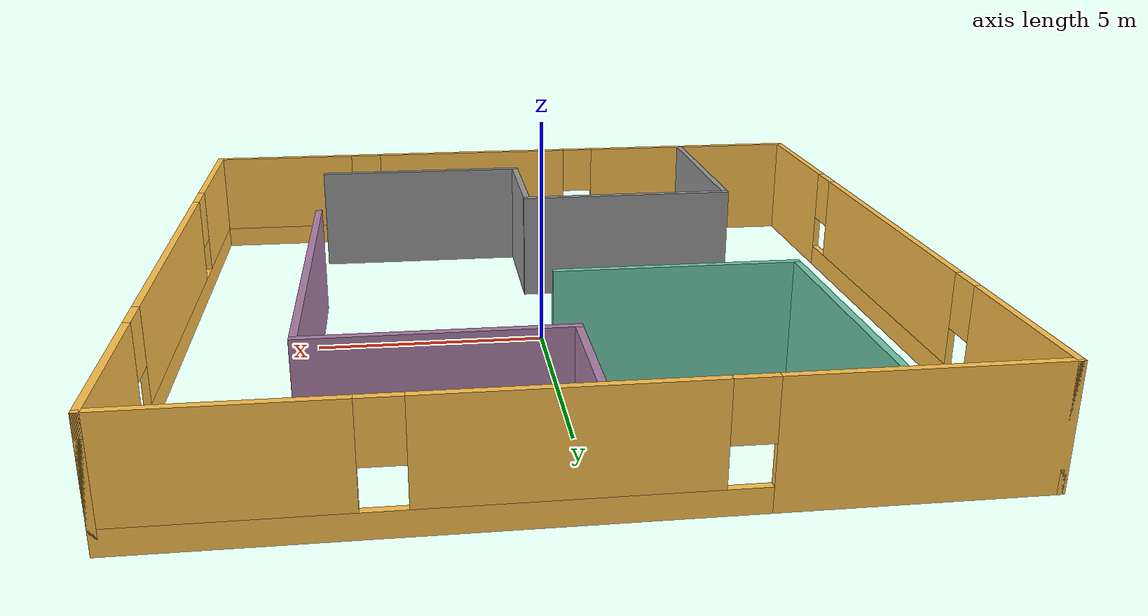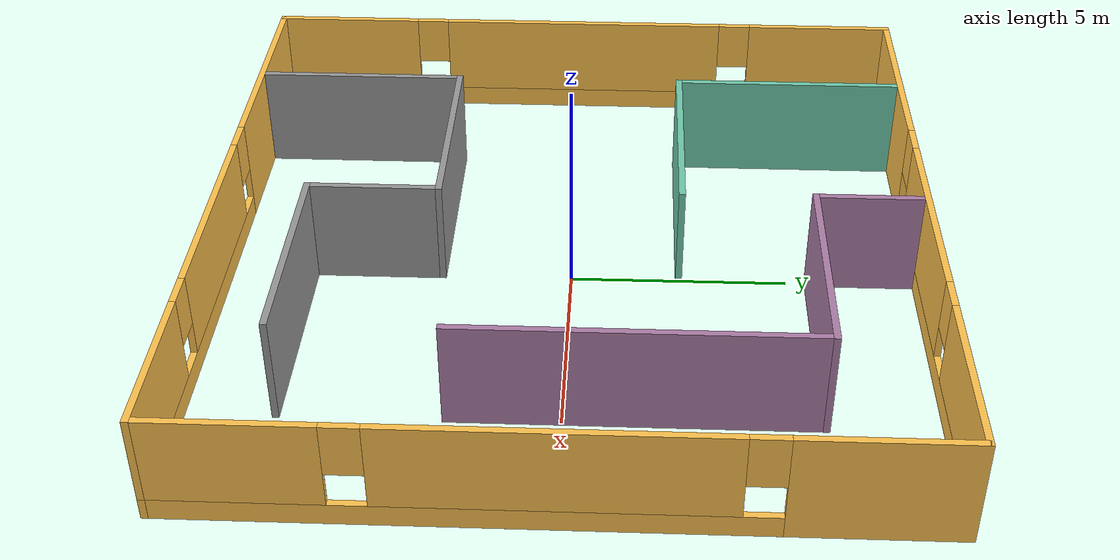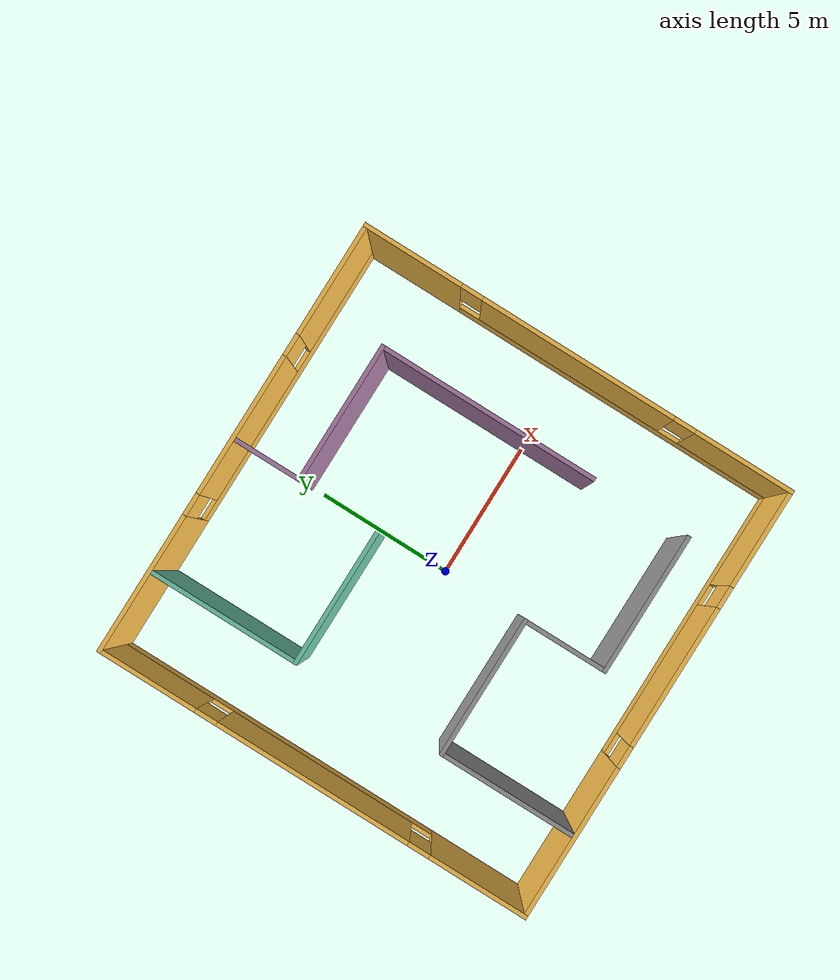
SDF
<?xml version='1.0'?>
<sdf version='1.7'>
  <model name='basic_office'>
    <link name='Wall_11'>
      <pose>8 0 0 0 0 -1.5708</pose>
      <self_collide>0</self_collide>
      <enable_wind>0</enable_wind>
      <kinematic>0</kinematic>
      <visual name='Wall_11_Visual_3'>
        <pose>6.2375 0 1.5 0 -0 0</pose>
        <geometry>
          <box>
            <size>3.675 0.15 2</size>
          </box>
        </geometry>
        <material>
          <script>
            <uri>file://media/materials/scripts/gazebo.material</uri>
            <name>Gazebo/Grey</name>
          </script>
          <ambient>1 0.764706 0.305882 1</ambient>
          <shader type='pixel'/>
        </material>
        <meta>
          <layer>0</layer>
        </meta>
        <transparency>0</transparency>
        <cast_shadows>1</cast_shadows>
      </visual>
      <visual name='Wall_11_Visual_5'>
        <pose>4 0 1.9 0 -0 0</pose>
        <geometry>
          <box>
            <size>0.8 0.15 1.2</size>
          </box>
        </geometry>
        <material>
          <script>
            <uri>file://media/materials/scripts/gazebo.material</uri>
            <name>Gazebo/Grey</name>
          </script>
          <ambient>1 0.764706 0.305882 1</ambient>
          <shader type='pixel'/>
        </material>
        <meta>
          <layer>0</layer>
        </meta>
        <transparency>0</transparency>
        <cast_shadows>1</cast_shadows>
      </visual>
      <visual name='Wall_11_Visual_2'>
        <pose>0 0 1.5 0 -0 0</pose>
        <geometry>
          <box>
            <size>7.2 0.15 2</size>
          </box>
        </geometry>
        <material>
          <script>
            <uri>file://media/materials/scripts/gazebo.material</uri>
            <name>Gazebo/Grey</name>
          </script>
          <ambient>1 0.764706 0.305882 1</ambient>
          <shader type='pixel'/>
        </material>
        <meta>
          <layer>0</layer>
        </meta>
        <transparency>0</transparency>
        <cast_shadows>1</cast_shadows>
      </visual>
      <visual name='Wall_11_Visual_0'>
        <pose>-6.2375 0 1.25 0 -0 0</pose>
        <geometry>
          <box>
            <size>3.675 0.15 2.5</size>
          </box>
        </geometry>
        <material>
          <script>
            <uri>file://media/materials/scripts/gazebo.material</uri>
            <name>Gazebo/Grey</name>
          </script>
          <ambient>1 0.764706 0.305882 1</ambient>
          <shader type='pixel'/>
        </material>
        <meta>
          <layer>0</layer>
        </meta>
        <transparency>0</transparency>
        <cast_shadows>1</cast_shadows>
      </visual>
      <visual name='Wall_11_Visual_4'>
        <pose>-4 0 1.9 0 -0 0</pose>
        <geometry>
          <box>
            <size>0.8 0.15 1.2</size>
          </box>
        </geometry>
        <material>
          <script>
            <uri>file://media/materials/scripts/gazebo.material</uri>
            <name>Gazebo/Grey</name>
          </script>
          <ambient>1 0.764706 0.305882 1</ambient>
          <shader type='pixel'/>
        </material>
        <meta>
          <layer>0</layer>
        </meta>
        <transparency>0</transparency>
        <cast_shadows>1</cast_shadows>
      </visual>
      <visual name='Wall_11_Visual_1'>
        <pose>1.8375 0 0.25 0 -0 0</pose>
        <geometry>
          <box>
            <size>12.475 0.15 0.5</size>
          </box>
        </geometry>
        <material>
          <script>
            <uri>file://media/materials/scripts/gazebo.material</uri>
            <name>Gazebo/Grey</name>
          </script>
          <ambient>1 0.764706 0.305882 1</ambient>
          <shader type='pixel'/>
        </material>
        <meta>
          <layer>0</layer>
        </meta>
        <transparency>0</transparency>
        <cast_shadows>1</cast_shadows>
      </visual>
      <collision name='Wall_11_Collision_0'>
        <laser_retro>0</laser_retro>
        <max_contacts>10</max_contacts>
        <pose>-6.2375 0 1.25 0 -0 0</pose>
        <geometry>
          <box>
            <size>3.675 0.15 2.5</size>
          </box>
        </geometry>
        <surface>
          <friction>
            <ode>
              <mu>1</mu>
              <mu2>1</mu2>
              <fdir1>0 0 0</fdir1>
              <slip1>0</slip1>
              <slip2>0</slip2>
            </ode>
            <torsional>
              <coefficient>1</coefficient>
              <patch_radius>0</patch_radius>
              <surface_radius>0</surface_radius>
              <use_patch_radius>1</use_patch_radius>
              <ode>
                <slip>0</slip>
              </ode>
            </torsional>
          </friction>
          <bounce>
            <restitution_coefficient>0</restitution_coefficient>
            <threshold>1e+06</threshold>
          </bounce>
          <contact>
            <collide_without_contact>0</collide_without_contact>
            <collide_without_contact_bitmask>1</collide_without_contact_bitmask>
            <collide_bitmask>1</collide_bitmask>
            <ode>
              <soft_cfm>0</soft_cfm>
              <soft_erp>0.2</soft_erp>
              <kp>1e+13</kp>
              <kd>1</kd>
              <max_vel>0.01</max_vel>
              <min_depth>0</min_depth>
            </ode>
            <bullet>
              <split_impulse>1</split_impulse>
              <split_impulse_penetration_threshold>-0.01</split_impulse_penetration_threshold>
              <soft_cfm>0</soft_cfm>
              <soft_erp>0.2</soft_erp>
              <kp>1e+13</kp>
              <kd>1</kd>
            </bullet>
          </contact>
        </surface>
      </collision>
      <collision name='Wall_11_Collision_3'>
        <laser_retro>0</laser_retro>
        <max_contacts>10</max_contacts>
        <pose>6.2375 0 1.5 0 -0 0</pose>
        <geometry>
          <box>
            <size>3.675 0.15 2</size>
          </box>
        </geometry>
        <surface>
          <friction>
            <ode>
              <mu>1</mu>
              <mu2>1</mu2>
              <fdir1>0 0 0</fdir1>
              <slip1>0</slip1>
              <slip2>0</slip2>
            </ode>
            <torsional>
              <coefficient>1</coefficient>
              <patch_radius>0</patch_radius>
              <surface_radius>0</surface_radius>
              <use_patch_radius>1</use_patch_radius>
              <ode>
                <slip>0</slip>
              </ode>
            </torsional>
          </friction>
          <bounce>
            <restitution_coefficient>0</restitution_coefficient>
            <threshold>1e+06</threshold>
          </bounce>
          <contact>
            <collide_without_contact>0</collide_without_contact>
            <collide_without_contact_bitmask>1</collide_without_contact_bitmask>
            <collide_bitmask>1</collide_bitmask>
            <ode>
              <soft_cfm>0</soft_cfm>
              <soft_erp>0.2</soft_erp>
              <kp>1e+13</kp>
              <kd>1</kd>
              <max_vel>0.01</max_vel>
              <min_depth>0</min_depth>
            </ode>
            <bullet>
              <split_impulse>1</split_impulse>
              <split_impulse_penetration_threshold>-0.01</split_impulse_penetration_threshold>
              <soft_cfm>0</soft_cfm>
              <soft_erp>0.2</soft_erp>
              <kp>1e+13</kp>
              <kd>1</kd>
            </bullet>
          </contact>
        </surface>
      </collision>
      <collision name='Wall_11_Collision_5'>
        <laser_retro>0</laser_retro>
        <max_contacts>10</max_contacts>
        <pose>4 0 1.9 0 -0 0</pose>
        <geometry>
          <box>
            <size>0.8 0.15 1.2</size>
          </box>
        </geometry>
        <surface>
          <friction>
            <ode>
              <mu>1</mu>
              <mu2>1</mu2>
              <fdir1>0 0 0</fdir1>
              <slip1>0</slip1>
              <slip2>0</slip2>
            </ode>
            <torsional>
              <coefficient>1</coefficient>
              <patch_radius>0</patch_radius>
              <surface_radius>0</surface_radius>
              <use_patch_radius>1</use_patch_radius>
              <ode>
                <slip>0</slip>
              </ode>
            </torsional>
          </friction>
          <bounce>
            <restitution_coefficient>0</restitution_coefficient>
            <threshold>1e+06</threshold>
          </bounce>
          <contact>
            <collide_without_contact>0</collide_without_contact>
            <collide_without_contact_bitmask>1</collide_without_contact_bitmask>
            <collide_bitmask>1</collide_bitmask>
            <ode>
              <soft_cfm>0</soft_cfm>
              <soft_erp>0.2</soft_erp>
              <kp>1e+13</kp>
              <kd>1</kd>
              <max_vel>0.01</max_vel>
              <min_depth>0</min_depth>
            </ode>
            <bullet>
              <split_impulse>1</split_impulse>
              <split_impulse_penetration_threshold>-0.01</split_impulse_penetration_threshold>
              <soft_cfm>0</soft_cfm>
              <soft_erp>0.2</soft_erp>
              <kp>1e+13</kp>
              <kd>1</kd>
            </bullet>
          </contact>
        </surface>
      </collision>
      <collision name='Wall_11_Collision_1'>
        <laser_retro>0</laser_retro>
        <max_contacts>10</max_contacts>
        <pose>1.8375 0 0.25 0 -0 0</pose>
        <geometry>
          <box>
            <size>12.475 0.15 0.5</size>
          </box>
        </geometry>
        <surface>
          <friction>
            <ode>
              <mu>1</mu>
              <mu2>1</mu2>
              <fdir1>0 0 0</fdir1>
              <slip1>0</slip1>
              <slip2>0</slip2>
            </ode>
            <torsional>
              <coefficient>1</coefficient>
              <patch_radius>0</patch_radius>
              <surface_radius>0</surface_radius>
              <use_patch_radius>1</use_patch_radius>
              <ode>
                <slip>0</slip>
              </ode>
            </torsional>
          </friction>
          <bounce>
            <restitution_coefficient>0</restitution_coefficient>
            <threshold>1e+06</threshold>
          </bounce>
          <contact>
            <collide_without_contact>0</collide_without_contact>
            <collide_without_contact_bitmask>1</collide_without_contact_bitmask>
            <collide_bitmask>1</collide_bitmask>
            <ode>
              <soft_cfm>0</soft_cfm>
              <soft_erp>0.2</soft_erp>
              <kp>1e+13</kp>
              <kd>1</kd>
              <max_vel>0.01</max_vel>
              <min_depth>0</min_depth>
            </ode>
            <bullet>
              <split_impulse>1</split_impulse>
              <split_impulse_penetration_threshold>-0.01</split_impulse_penetration_threshold>
              <soft_cfm>0</soft_cfm>
              <soft_erp>0.2</soft_erp>
              <kp>1e+13</kp>
              <kd>1</kd>
            </bullet>
          </contact>
        </surface>
      </collision>
      <collision name='Wall_11_Collision_4'>
        <laser_retro>0</laser_retro>
        <max_contacts>10</max_contacts>
        <pose>-4 0 1.9 0 -0 0</pose>
        <geometry>
          <box>
            <size>0.8 0.15 1.2</size>
          </box>
        </geometry>
        <surface>
          <friction>
            <ode>
              <mu>1</mu>
              <mu2>1</mu2>
              <fdir1>0 0 0</fdir1>
              <slip1>0</slip1>
              <slip2>0</slip2>
            </ode>
            <torsional>
              <coefficient>1</coefficient>
              <patch_radius>0</patch_radius>
              <surface_radius>0</surface_radius>
              <use_patch_radius>1</use_patch_radius>
              <ode>
                <slip>0</slip>
              </ode>
            </torsional>
          </friction>
          <bounce>
            <restitution_coefficient>0</restitution_coefficient>
            <threshold>1e+06</threshold>
          </bounce>
          <contact>
            <collide_without_contact>0</collide_without_contact>
            <collide_without_contact_bitmask>1</collide_without_contact_bitmask>
            <collide_bitmask>1</collide_bitmask>
            <ode>
              <soft_cfm>0</soft_cfm>
              <soft_erp>0.2</soft_erp>
              <kp>1e+13</kp>
              <kd>1</kd>
              <max_vel>0.01</max_vel>
              <min_depth>0</min_depth>
            </ode>
            <bullet>
              <split_impulse>1</split_impulse>
              <split_impulse_penetration_threshold>-0.01</split_impulse_penetration_threshold>
              <soft_cfm>0</soft_cfm>
              <soft_erp>0.2</soft_erp>
              <kp>1e+13</kp>
              <kd>1</kd>
            </bullet>
          </contact>
        </surface>
      </collision>
      <collision name='Wall_11_Collision_2'>
        <laser_retro>0</laser_retro>
        <max_contacts>10</max_contacts>
        <pose>0 0 1.5 0 -0 0</pose>
        <geometry>
          <box>
            <size>7.2 0.15 2</size>
          </box>
        </geometry>
        <surface>
          <friction>
            <ode>
              <mu>1</mu>
              <mu2>1</mu2>
              <fdir1>0 0 0</fdir1>
              <slip1>0</slip1>
              <slip2>0</slip2>
            </ode>
            <torsional>
              <coefficient>1</coefficient>
              <patch_radius>0</patch_radius>
              <surface_radius>0</surface_radius>
              <use_patch_radius>1</use_patch_radius>
              <ode>
                <slip>0</slip>
              </ode>
            </torsional>
          </friction>
          <bounce>
            <restitution_coefficient>0</restitution_coefficient>
            <threshold>1e+06</threshold>
          </bounce>
          <contact>
            <collide_without_contact>0</collide_without_contact>
            <collide_without_contact_bitmask>1</collide_without_contact_bitmask>
            <collide_bitmask>1</collide_bitmask>
            <ode>
              <soft_cfm>0</soft_cfm>
              <soft_erp>0.2</soft_erp>
              <kp>1e+13</kp>
              <kd>1</kd>
              <max_vel>0.01</max_vel>
              <min_depth>0</min_depth>
            </ode>
            <bullet>
              <split_impulse>1</split_impulse>
              <split_impulse_penetration_threshold>-0.01</split_impulse_penetration_threshold>
              <soft_cfm>0</soft_cfm>
              <soft_erp>0.2</soft_erp>
              <kp>1e+13</kp>
              <kd>1</kd>
            </bullet>
          </contact>
        </surface>
      </collision>
    </link>
    <link name='Wall_15'>
      <pose>0 8 0 0 -0 0</pose>
      <self_collide>0</self_collide>
      <enable_wind>0</enable_wind>
      <kinematic>0</kinematic>
      <visual name='Wall_15_Visual_2'>
        <pose>0.5 0 1.5 0 -0 0</pose>
        <geometry>
          <box>
            <size>5.2 0.15 2</size>
          </box>
        </geometry>
        <material>
          <script>
            <uri>file://media/materials/scripts/gazebo.material</uri>
            <name>Gazebo/Grey</name>
          </script>
          <ambient>1 0.764706 0.305882 1</ambient>
          <shader type='pixel'/>
        </material>
        <meta>
          <layer>0</layer>
        </meta>
        <transparency>0</transparency>
        <cast_shadows>1</cast_shadows>
      </visual>
      <visual name='Wall_15_Visual_4'>
        <pose>-2.5 0 1.9 0 -0 0</pose>
        <geometry>
          <box>
            <size>0.8 0.15 1.2</size>
          </box>
        </geometry>
        <material>
          <script>
            <uri>file://media/materials/scripts/gazebo.material</uri>
            <name>Gazebo/Grey</name>
          </script>
          <ambient>1 0.764706 0.305882 1</ambient>
          <shader type='pixel'/>
        </material>
        <meta>
          <layer>0</layer>
        </meta>
        <transparency>0</transparency>
        <cast_shadows>1</cast_shadows>
      </visual>
      <visual name='Wall_15_Visual_5'>
        <pose>3.5 0 1.9 0 -0 0</pose>
        <geometry>
          <box>
            <size>0.8 0.15 1.2</size>
          </box>
        </geometry>
        <material>
          <script>
            <uri>file://media/materials/scripts/gazebo.material</uri>
            <name>Gazebo/Grey</name>
          </script>
          <ambient>1 0.764706 0.305882 1</ambient>
          <shader type='pixel'/>
        </material>
        <meta>
          <layer>0</layer>
        </meta>
        <transparency>0</transparency>
        <cast_shadows>1</cast_shadows>
      </visual>
      <visual name='Wall_15_Visual_3'>
        <pose>5.9875 0 1.5 0 -0 0</pose>
        <geometry>
          <box>
            <size>4.175 0.15 2</size>
          </box>
        </geometry>
        <material>
          <script>
            <uri>file://media/materials/scripts/gazebo.material</uri>
            <name>Gazebo/Grey</name>
          </script>
          <ambient>1 0.764706 0.305882 1</ambient>
          <shader type='pixel'/>
        </material>
        <meta>
          <layer>0</layer>
        </meta>
        <transparency>0</transparency>
        <cast_shadows>1</cast_shadows>
      </visual>
      <visual name='Wall_15_Visual_1'>
        <pose>2.5875 0 0.25 0 -0 0</pose>
        <geometry>
          <box>
            <size>10.975 0.15 0.5</size>
          </box>
        </geometry>
        <material>
          <script>
            <uri>file://media/materials/scripts/gazebo.material</uri>
            <name>Gazebo/Grey</name>
          </script>
          <ambient>1 0.764706 0.305882 1</ambient>
          <shader type='pixel'/>
        </material>
        <meta>
          <layer>0</layer>
        </meta>
        <transparency>0</transparency>
        <cast_shadows>1</cast_shadows>
      </visual>
      <visual name='Wall_15_Visual_0'>
        <pose>-5.4875 0 1.25 0 -0 0</pose>
        <geometry>
          <box>
            <size>5.175 0.15 2.5</size>
          </box>
        </geometry>
        <material>
          <script>
            <uri>file://media/materials/scripts/gazebo.material</uri>
            <name>Gazebo/Grey</name>
          </script>
          <ambient>1 0.764706 0.305882 1</ambient>
          <shader type='pixel'/>
        </material>
        <meta>
          <layer>0</layer>
        </meta>
        <transparency>0</transparency>
        <cast_shadows>1</cast_shadows>
      </visual>
      <collision name='Wall_15_Collision_0'>
        <laser_retro>0</laser_retro>
        <max_contacts>10</max_contacts>
        <pose>-5.4875 0 1.25 0 -0 0</pose>
        <geometry>
          <box>
            <size>5.175 0.15 2.5</size>
          </box>
        </geometry>
        <surface>
          <friction>
            <ode>
              <mu>1</mu>
              <mu2>1</mu2>
              <fdir1>0 0 0</fdir1>
              <slip1>0</slip1>
              <slip2>0</slip2>
            </ode>
            <torsional>
              <coefficient>1</coefficient>
              <patch_radius>0</patch_radius>
              <surface_radius>0</surface_radius>
              <use_patch_radius>1</use_patch_radius>
              <ode>
                <slip>0</slip>
              </ode>
            </torsional>
          </friction>
          <bounce>
            <restitution_coefficient>0</restitution_coefficient>
            <threshold>1e+06</threshold>
          </bounce>
          <contact>
            <collide_without_contact>0</collide_without_contact>
            <collide_without_contact_bitmask>1</collide_without_contact_bitmask>
            <collide_bitmask>1</collide_bitmask>
            <ode>
              <soft_cfm>0</soft_cfm>
              <soft_erp>0.2</soft_erp>
              <kp>1e+13</kp>
              <kd>1</kd>
              <max_vel>0.01</max_vel>
              <min_depth>0</min_depth>
            </ode>
            <bullet>
              <split_impulse>1</split_impulse>
              <split_impulse_penetration_threshold>-0.01</split_impulse_penetration_threshold>
              <soft_cfm>0</soft_cfm>
              <soft_erp>0.2</soft_erp>
              <kp>1e+13</kp>
              <kd>1</kd>
            </bullet>
          </contact>
        </surface>
      </collision>
      <collision name='Wall_15_Collision_5'>
        <laser_retro>0</laser_retro>
        <max_contacts>10</max_contacts>
        <pose>3.5 0 1.9 0 -0 0</pose>
        <geometry>
          <box>
            <size>0.8 0.15 1.2</size>
          </box>
        </geometry>
        <surface>
          <friction>
            <ode>
              <mu>1</mu>
              <mu2>1</mu2>
              <fdir1>0 0 0</fdir1>
              <slip1>0</slip1>
              <slip2>0</slip2>
            </ode>
            <torsional>
              <coefficient>1</coefficient>
              <patch_radius>0</patch_radius>
              <surface_radius>0</surface_radius>
              <use_patch_radius>1</use_patch_radius>
              <ode>
                <slip>0</slip>
              </ode>
            </torsional>
          </friction>
          <bounce>
            <restitution_coefficient>0</restitution_coefficient>
            <threshold>1e+06</threshold>
          </bounce>
          <contact>
            <collide_without_contact>0</collide_without_contact>
            <collide_without_contact_bitmask>1</collide_without_contact_bitmask>
            <collide_bitmask>1</collide_bitmask>
            <ode>
              <soft_cfm>0</soft_cfm>
              <soft_erp>0.2</soft_erp>
              <kp>1e+13</kp>
              <kd>1</kd>
              <max_vel>0.01</max_vel>
              <min_depth>0</min_depth>
            </ode>
            <bullet>
              <split_impulse>1</split_impulse>
              <split_impulse_penetration_threshold>-0.01</split_impulse_penetration_threshold>
              <soft_cfm>0</soft_cfm>
              <soft_erp>0.2</soft_erp>
              <kp>1e+13</kp>
              <kd>1</kd>
            </bullet>
          </contact>
        </surface>
      </collision>
      <collision name='Wall_15_Collision_2'>
        <laser_retro>0</laser_retro>
        <max_contacts>10</max_contacts>
        <pose>0.5 0 1.5 0 -0 0</pose>
        <geometry>
          <box>
            <size>5.2 0.15 2</size>
          </box>
        </geometry>
        <surface>
          <friction>
            <ode>
              <mu>1</mu>
              <mu2>1</mu2>
              <fdir1>0 0 0</fdir1>
              <slip1>0</slip1>
              <slip2>0</slip2>
            </ode>
            <torsional>
              <coefficient>1</coefficient>
              <patch_radius>0</patch_radius>
              <surface_radius>0</surface_radius>
              <use_patch_radius>1</use_patch_radius>
              <ode>
                <slip>0</slip>
              </ode>
            </torsional>
          </friction>
          <bounce>
            <restitution_coefficient>0</restitution_coefficient>
            <threshold>1e+06</threshold>
          </bounce>
          <contact>
            <collide_without_contact>0</collide_without_contact>
            <collide_without_contact_bitmask>1</collide_without_contact_bitmask>
            <collide_bitmask>1</collide_bitmask>
            <ode>
              <soft_cfm>0</soft_cfm>
              <soft_erp>0.2</soft_erp>
              <kp>1e+13</kp>
              <kd>1</kd>
              <max_vel>0.01</max_vel>
              <min_depth>0</min_depth>
            </ode>
            <bullet>
              <split_impulse>1</split_impulse>
              <split_impulse_penetration_threshold>-0.01</split_impulse_penetration_threshold>
              <soft_cfm>0</soft_cfm>
              <soft_erp>0.2</soft_erp>
              <kp>1e+13</kp>
              <kd>1</kd>
            </bullet>
          </contact>
        </surface>
      </collision>
      <collision name='Wall_15_Collision_3'>
        <laser_retro>0</laser_retro>
        <max_contacts>10</max_contacts>
        <pose>5.9875 0 1.5 0 -0 0</pose>
        <geometry>
          <box>
            <size>4.175 0.15 2</size>
          </box>
        </geometry>
        <surface>
          <friction>
            <ode>
              <mu>1</mu>
              <mu2>1</mu2>
              <fdir1>0 0 0</fdir1>
              <slip1>0</slip1>
              <slip2>0</slip2>
            </ode>
            <torsional>
              <coefficient>1</coefficient>
              <patch_radius>0</patch_radius>
              <surface_radius>0</surface_radius>
              <use_patch_radius>1</use_patch_radius>
              <ode>
                <slip>0</slip>
              </ode>
            </torsional>
          </friction>
          <bounce>
            <restitution_coefficient>0</restitution_coefficient>
            <threshold>1e+06</threshold>
          </bounce>
          <contact>
            <collide_without_contact>0</collide_without_contact>
            <collide_without_contact_bitmask>1</collide_without_contact_bitmask>
            <collide_bitmask>1</collide_bitmask>
            <ode>
              <soft_cfm>0</soft_cfm>
              <soft_erp>0.2</soft_erp>
              <kp>1e+13</kp>
              <kd>1</kd>
              <max_vel>0.01</max_vel>
              <min_depth>0</min_depth>
            </ode>
            <bullet>
              <split_impulse>1</split_impulse>
              <split_impulse_penetration_threshold>-0.01</split_impulse_penetration_threshold>
              <soft_cfm>0</soft_cfm>
              <soft_erp>0.2</soft_erp>
              <kp>1e+13</kp>
              <kd>1</kd>
            </bullet>
          </contact>
        </surface>
      </collision>
      <collision name='Wall_15_Collision_1'>
        <laser_retro>0</laser_retro>
        <max_contacts>10</max_contacts>
        <pose>2.5875 0 0.25 0 -0 0</pose>
        <geometry>
          <box>
            <size>10.975 0.15 0.5</size>
          </box>
        </geometry>
        <surface>
          <friction>
            <ode>
              <mu>1</mu>
              <mu2>1</mu2>
              <fdir1>0 0 0</fdir1>
              <slip1>0</slip1>
              <slip2>0</slip2>
            </ode>
            <torsional>
              <coefficient>1</coefficient>
              <patch_radius>0</patch_radius>
              <surface_radius>0</surface_radius>
              <use_patch_radius>1</use_patch_radius>
              <ode>
                <slip>0</slip>
              </ode>
            </torsional>
          </friction>
          <bounce>
            <restitution_coefficient>0</restitution_coefficient>
            <threshold>1e+06</threshold>
          </bounce>
          <contact>
            <collide_without_contact>0</collide_without_contact>
            <collide_without_contact_bitmask>1</collide_without_contact_bitmask>
            <collide_bitmask>1</collide_bitmask>
            <ode>
              <soft_cfm>0</soft_cfm>
              <soft_erp>0.2</soft_erp>
              <kp>1e+13</kp>
              <kd>1</kd>
              <max_vel>0.01</max_vel>
              <min_depth>0</min_depth>
            </ode>
            <bullet>
              <split_impulse>1</split_impulse>
              <split_impulse_penetration_threshold>-0.01</split_impulse_penetration_threshold>
              <soft_cfm>0</soft_cfm>
              <soft_erp>0.2</soft_erp>
              <kp>1e+13</kp>
              <kd>1</kd>
            </bullet>
          </contact>
        </surface>
      </collision>
      <collision name='Wall_15_Collision_4'>
        <laser_retro>0</laser_retro>
        <max_contacts>10</max_contacts>
        <pose>-2.5 0 1.9 0 -0 0</pose>
        <geometry>
          <box>
            <size>0.8 0.15 1.2</size>
          </box>
        </geometry>
        <surface>
          <friction>
            <ode>
              <mu>1</mu>
              <mu2>1</mu2>
              <fdir1>0 0 0</fdir1>
              <slip1>0</slip1>
              <slip2>0</slip2>
            </ode>
            <torsional>
              <coefficient>1</coefficient>
              <patch_radius>0</patch_radius>
              <surface_radius>0</surface_radius>
              <use_patch_radius>1</use_patch_radius>
              <ode>
                <slip>0</slip>
              </ode>
            </torsional>
          </friction>
          <bounce>
            <restitution_coefficient>0</restitution_coefficient>
            <threshold>1e+06</threshold>
          </bounce>
          <contact>
            <collide_without_contact>0</collide_without_contact>
            <collide_without_contact_bitmask>1</collide_without_contact_bitmask>
            <collide_bitmask>1</collide_bitmask>
            <ode>
              <soft_cfm>0</soft_cfm>
              <soft_erp>0.2</soft_erp>
              <kp>1e+13</kp>
              <kd>1</kd>
              <max_vel>0.01</max_vel>
              <min_depth>0</min_depth>
            </ode>
            <bullet>
              <split_impulse>1</split_impulse>
              <split_impulse_penetration_threshold>-0.01</split_impulse_penetration_threshold>
              <soft_cfm>0</soft_cfm>
              <soft_erp>0.2</soft_erp>
              <kp>1e+13</kp>
              <kd>1</kd>
            </bullet>
          </contact>
        </surface>
      </collision>
    </link>
    <link name='Wall_17'>
      <pose>-8 0 0 0 -0 1.5708</pose>
      <self_collide>0</self_collide>
      <enable_wind>0</enable_wind>
      <kinematic>0</kinematic>
      <gravity>1</gravity>
      <inertial>
        <mass>1</mass>
        <pose>0 0 0 0 -0 0</pose>
        <inertia>
          <ixx>1</ixx>
          <ixy>0</ixy>
          <ixz>0</ixz>
          <iyy>1</iyy>
          <iyz>0</iyz>
          <izz>1</izz>
        </inertia>
      </inertial>
      <visual name='Wall_17_Visual_1'>
        <pose>1.8375 0 0.25 0 -0 0</pose>
        <geometry>
          <box>
            <size>12.475 0.15 0.5</size>
          </box>
        </geometry>
        <material>
          <script>
            <uri>file://media/materials/scripts/gazebo.material</uri>
            <name>Gazebo/Grey</name>
          </script>
          <ambient>1 0.765 0.306 1</ambient>
          <shader type='pixel'>
            <normal_map>__default__</normal_map>
          </shader>
          <diffuse>0.7 0.7 0.7 1</diffuse>
          <specular>0.01 0.01 0.01 1</specular>
          <emissive>0 0 0 1</emissive>
        </material>
        <meta>
          <layer>0</layer>
        </meta>
        <transparency>0</transparency>
        <cast_shadows>1</cast_shadows>
      </visual>
      <visual name='Wall_17_Visual_2'>
        <pose>0 0 1.5 0 -0 0</pose>
        <geometry>
          <box>
            <size>7.2 0.15 2</size>
          </box>
        </geometry>
        <material>
          <script>
            <uri>file://media/materials/scripts/gazebo.material</uri>
            <name>Gazebo/Grey</name>
          </script>
          <ambient>1 0.765 0.306 1</ambient>
          <shader type='pixel'>
            <normal_map>__default__</normal_map>
          </shader>
          <diffuse>0.7 0.7 0.7 1</diffuse>
          <specular>0.01 0.01 0.01 1</specular>
          <emissive>0 0 0 1</emissive>
        </material>
        <meta>
          <layer>0</layer>
        </meta>
        <transparency>0</transparency>
        <cast_shadows>1</cast_shadows>
      </visual>
      <visual name='Wall_17_Visual_0'>
        <pose>-6.2375 0 1.25 0 -0 0</pose>
        <geometry>
          <box>
            <size>3.675 0.15 2.5</size>
          </box>
        </geometry>
        <material>
          <script>
            <uri>file://media/materials/scripts/gazebo.material</uri>
            <name>Gazebo/Grey</name>
          </script>
          <ambient>1 0.765 0.306 1</ambient>
          <shader type='pixel'>
            <normal_map>__default__</normal_map>
          </shader>
          <diffuse>0.7 0.7 0.7 1</diffuse>
          <specular>0.01 0.01 0.01 1</specular>
          <emissive>0 0 0 1</emissive>
        </material>
        <meta>
          <layer>0</layer>
        </meta>
        <transparency>0</transparency>
        <cast_shadows>1</cast_shadows>
      </visual>
      <visual name='Wall_17_Visual_5'>
        <pose>4 0 1.9 0 -0 0</pose>
        <geometry>
          <box>
            <size>0.8 0.15 1.2</size>
          </box>
        </geometry>
        <material>
          <script>
            <uri>file://media/materials/scripts/gazebo.material</uri>
            <name>Gazebo/Grey</name>
          </script>
          <ambient>1 0.765 0.306 1</ambient>
          <shader type='pixel'>
            <normal_map>__default__</normal_map>
          </shader>
          <diffuse>0.7 0.7 0.7 1</diffuse>
          <specular>0.01 0.01 0.01 1</specular>
          <emissive>0 0 0 1</emissive>
        </material>
        <meta>
          <layer>0</layer>
        </meta>
        <transparency>0</transparency>
        <cast_shadows>1</cast_shadows>
      </visual>
      <visual name='Wall_17_Visual_3'>
        <pose>6.2375 0 1.5 0 -0 0</pose>
        <geometry>
          <box>
            <size>3.675 0.15 2</size>
          </box>
        </geometry>
        <material>
          <script>
            <uri>file://media/materials/scripts/gazebo.material</uri>
            <name>Gazebo/Grey</name>
          </script>
          <ambient>1 0.765 0.306 1</ambient>
          <shader type='pixel'>
            <normal_map>__default__</normal_map>
          </shader>
          <diffuse>0.7 0.7 0.7 1</diffuse>
          <specular>0.01 0.01 0.01 1</specular>
          <emissive>0 0 0 1</emissive>
        </material>
        <meta>
          <layer>0</layer>
        </meta>
        <transparency>0</transparency>
        <cast_shadows>1</cast_shadows>
      </visual>
      <visual name='Wall_17_Visual_4'>
        <pose>-4 0 1.9 0 -0 0</pose>
        <geometry>
          <box>
            <size>0.8 0.15 1.2</size>
          </box>
        </geometry>
        <material>
          <script>
            <uri>file://media/materials/scripts/gazebo.material</uri>
            <name>Gazebo/Grey</name>
          </script>
          <ambient>1 0.765 0.306 1</ambient>
          <shader type='pixel'>
            <normal_map>__default__</normal_map>
          </shader>
          <diffuse>0.7 0.7 0.7 1</diffuse>
          <specular>0.01 0.01 0.01 1</specular>
          <emissive>0 0 0 1</emissive>
        </material>
        <meta>
          <layer>0</layer>
        </meta>
        <transparency>0</transparency>
        <cast_shadows>1</cast_shadows>
      </visual>
      <collision name='Wall_17_Collision_3'>
        <laser_retro>0</laser_retro>
        <max_contacts>10</max_contacts>
        <pose>6.2375 0 1.5 0 -0 0</pose>
        <geometry>
          <box>
            <size>3.675 0.15 2</size>
          </box>
        </geometry>
        <surface>
          <friction>
            <ode>
              <mu>1</mu>
              <mu2>1</mu2>
              <fdir1>0 0 0</fdir1>
              <slip1>0</slip1>
              <slip2>0</slip2>
            </ode>
            <torsional>
              <coefficient>1</coefficient>
              <patch_radius>0</patch_radius>
              <surface_radius>0</surface_radius>
              <use_patch_radius>1</use_patch_radius>
              <ode>
                <slip>0</slip>
              </ode>
            </torsional>
          </friction>
          <bounce>
            <restitution_coefficient>0</restitution_coefficient>
            <threshold>1e+06</threshold>
          </bounce>
          <contact>
            <collide_without_contact>0</collide_without_contact>
            <collide_without_contact_bitmask>1</collide_without_contact_bitmask>
            <collide_bitmask>1</collide_bitmask>
            <ode>
              <soft_cfm>0</soft_cfm>
              <soft_erp>0.2</soft_erp>
              <kp>1e+13</kp>
              <kd>1</kd>
              <max_vel>0.01</max_vel>
              <min_depth>0</min_depth>
            </ode>
            <bullet>
              <split_impulse>1</split_impulse>
              <split_impulse_penetration_threshold>-0.01</split_impulse_penetration_threshold>
              <soft_cfm>0</soft_cfm>
              <soft_erp>0.2</soft_erp>
              <kp>1e+13</kp>
              <kd>1</kd>
            </bullet>
          </contact>
        </surface>
      </collision>
      <collision name='Wall_17_Collision_5'>
        <laser_retro>0</laser_retro>
        <max_contacts>10</max_contacts>
        <pose>4 0 1.9 0 -0 0</pose>
        <geometry>
          <box>
            <size>0.8 0.15 1.2</size>
          </box>
        </geometry>
        <surface>
          <friction>
            <ode>
              <mu>1</mu>
              <mu2>1</mu2>
              <fdir1>0 0 0</fdir1>
              <slip1>0</slip1>
              <slip2>0</slip2>
            </ode>
            <torsional>
              <coefficient>1</coefficient>
              <patch_radius>0</patch_radius>
              <surface_radius>0</surface_radius>
              <use_patch_radius>1</use_patch_radius>
              <ode>
                <slip>0</slip>
              </ode>
            </torsional>
          </friction>
          <bounce>
            <restitution_coefficient>0</restitution_coefficient>
            <threshold>1e+06</threshold>
          </bounce>
          <contact>
            <collide_without_contact>0</collide_without_contact>
            <collide_without_contact_bitmask>1</collide_without_contact_bitmask>
            <collide_bitmask>1</collide_bitmask>
            <ode>
              <soft_cfm>0</soft_cfm>
              <soft_erp>0.2</soft_erp>
              <kp>1e+13</kp>
              <kd>1</kd>
              <max_vel>0.01</max_vel>
              <min_depth>0</min_depth>
            </ode>
            <bullet>
              <split_impulse>1</split_impulse>
              <split_impulse_penetration_threshold>-0.01</split_impulse_penetration_threshold>
              <soft_cfm>0</soft_cfm>
              <soft_erp>0.2</soft_erp>
              <kp>1e+13</kp>
              <kd>1</kd>
            </bullet>
          </contact>
        </surface>
      </collision>
      <collision name='Wall_17_Collision_4'>
        <laser_retro>0</laser_retro>
        <max_contacts>10</max_contacts>
        <pose>-4 0 1.9 0 -0 0</pose>
        <geometry>
          <box>
            <size>0.8 0.15 1.2</size>
          </box>
        </geometry>
        <surface>
          <friction>
            <ode>
              <mu>1</mu>
              <mu2>1</mu2>
              <fdir1>0 0 0</fdir1>
              <slip1>0</slip1>
              <slip2>0</slip2>
            </ode>
            <torsional>
              <coefficient>1</coefficient>
              <patch_radius>0</patch_radius>
              <surface_radius>0</surface_radius>
              <use_patch_radius>1</use_patch_radius>
              <ode>
                <slip>0</slip>
              </ode>
            </torsional>
          </friction>
          <bounce>
            <restitution_coefficient>0</restitution_coefficient>
            <threshold>1e+06</threshold>
          </bounce>
          <contact>
            <collide_without_contact>0</collide_without_contact>
            <collide_without_contact_bitmask>1</collide_without_contact_bitmask>
            <collide_bitmask>1</collide_bitmask>
            <ode>
              <soft_cfm>0</soft_cfm>
              <soft_erp>0.2</soft_erp>
              <kp>1e+13</kp>
              <kd>1</kd>
              <max_vel>0.01</max_vel>
              <min_depth>0</min_depth>
            </ode>
            <bullet>
              <split_impulse>1</split_impulse>
              <split_impulse_penetration_threshold>-0.01</split_impulse_penetration_threshold>
              <soft_cfm>0</soft_cfm>
              <soft_erp>0.2</soft_erp>
              <kp>1e+13</kp>
              <kd>1</kd>
            </bullet>
          </contact>
        </surface>
      </collision>
      <collision name='Wall_17_Collision_0'>
        <laser_retro>0</laser_retro>
        <max_contacts>10</max_contacts>
        <pose>-6.2375 0 1.25 0 -0 0</pose>
        <geometry>
          <box>
            <size>3.675 0.15 2.5</size>
          </box>
        </geometry>
        <surface>
          <friction>
            <ode>
              <mu>1</mu>
              <mu2>1</mu2>
              <fdir1>0 0 0</fdir1>
              <slip1>0</slip1>
              <slip2>0</slip2>
            </ode>
            <torsional>
              <coefficient>1</coefficient>
              <patch_radius>0</patch_radius>
              <surface_radius>0</surface_radius>
              <use_patch_radius>1</use_patch_radius>
              <ode>
                <slip>0</slip>
              </ode>
            </torsional>
          </friction>
          <bounce>
            <restitution_coefficient>0</restitution_coefficient>
            <threshold>1e+06</threshold>
          </bounce>
          <contact>
            <collide_without_contact>0</collide_without_contact>
            <collide_without_contact_bitmask>1</collide_without_contact_bitmask>
            <collide_bitmask>1</collide_bitmask>
            <ode>
              <soft_cfm>0</soft_cfm>
              <soft_erp>0.2</soft_erp>
              <kp>1e+13</kp>
              <kd>1</kd>
              <max_vel>0.01</max_vel>
              <min_depth>0</min_depth>
            </ode>
            <bullet>
              <split_impulse>1</split_impulse>
              <split_impulse_penetration_threshold>-0.01</split_impulse_penetration_threshold>
              <soft_cfm>0</soft_cfm>
              <soft_erp>0.2</soft_erp>
              <kp>1e+13</kp>
              <kd>1</kd>
            </bullet>
          </contact>
        </surface>
      </collision>
      <collision name='Wall_17_Collision_1'>
        <laser_retro>0</laser_retro>
        <max_contacts>10</max_contacts>
        <pose>1.8375 0 0.25 0 -0 0</pose>
        <geometry>
          <box>
            <size>12.475 0.15 0.5</size>
          </box>
        </geometry>
        <surface>
          <friction>
            <ode>
              <mu>1</mu>
              <mu2>1</mu2>
              <fdir1>0 0 0</fdir1>
              <slip1>0</slip1>
              <slip2>0</slip2>
            </ode>
            <torsional>
              <coefficient>1</coefficient>
              <patch_radius>0</patch_radius>
              <surface_radius>0</surface_radius>
              <use_patch_radius>1</use_patch_radius>
              <ode>
                <slip>0</slip>
              </ode>
            </torsional>
          </friction>
          <bounce>
            <restitution_coefficient>0</restitution_coefficient>
            <threshold>1e+06</threshold>
          </bounce>
          <contact>
            <collide_without_contact>0</collide_without_contact>
            <collide_without_contact_bitmask>1</collide_without_contact_bitmask>
            <collide_bitmask>1</collide_bitmask>
            <ode>
              <soft_cfm>0</soft_cfm>
              <soft_erp>0.2</soft_erp>
              <kp>1e+13</kp>
              <kd>1</kd>
              <max_vel>0.01</max_vel>
              <min_depth>0</min_depth>
            </ode>
            <bullet>
              <split_impulse>1</split_impulse>
              <split_impulse_penetration_threshold>-0.01</split_impulse_penetration_threshold>
              <soft_cfm>0</soft_cfm>
              <soft_erp>0.2</soft_erp>
              <kp>1e+13</kp>
              <kd>1</kd>
            </bullet>
          </contact>
        </surface>
      </collision>
      <collision name='Wall_17_Collision_2'>
        <laser_retro>0</laser_retro>
        <max_contacts>10</max_contacts>
        <pose>0 0 1.5 0 -0 0</pose>
        <geometry>
          <box>
            <size>7.2 0.15 2</size>
          </box>
        </geometry>
        <surface>
          <friction>
            <ode>
              <mu>1</mu>
              <mu2>1</mu2>
              <fdir1>0 0 0</fdir1>
              <slip1>0</slip1>
              <slip2>0</slip2>
            </ode>
            <torsional>
              <coefficient>1</coefficient>
              <patch_radius>0</patch_radius>
              <surface_radius>0</surface_radius>
              <use_patch_radius>1</use_patch_radius>
              <ode>
                <slip>0</slip>
              </ode>
            </torsional>
          </friction>
          <bounce>
            <restitution_coefficient>0</restitution_coefficient>
            <threshold>1e+06</threshold>
          </bounce>
          <contact>
            <collide_without_contact>0</collide_without_contact>
            <collide_without_contact_bitmask>1</collide_without_contact_bitmask>
            <collide_bitmask>1</collide_bitmask>
            <ode>
              <soft_cfm>0</soft_cfm>
              <soft_erp>0.2</soft_erp>
              <kp>1e+13</kp>
              <kd>1</kd>
              <max_vel>0.01</max_vel>
              <min_depth>0</min_depth>
            </ode>
            <bullet>
              <split_impulse>1</split_impulse>
              <split_impulse_penetration_threshold>-0.01</split_impulse_penetration_threshold>
              <soft_cfm>0</soft_cfm>
              <soft_erp>0.2</soft_erp>
              <kp>1e+13</kp>
              <kd>1</kd>
            </bullet>
          </contact>
        </surface>
      </collision>
    </link>
    <link name='Wall_20'>
      <pose>0 -8 0 0 -0 0</pose>
      <self_collide>0</self_collide>
      <enable_wind>0</enable_wind>
      <kinematic>0</kinematic>
      <visual name='Wall_20_Visual_0'>
        <pose>-5.2375 0 1.25 0 -0 0</pose>
        <geometry>
          <box>
            <size>5.675 0.15 2.5</size>
          </box>
        </geometry>
        <material>
          <script>
            <uri>file://media/materials/scripts/gazebo.material</uri>
            <name>Gazebo/Grey</name>
          </script>
          <ambient>1 0.764706 0.305882 1</ambient>
          <shader type='pixel'/>
        </material>
        <meta>
          <layer>0</layer>
        </meta>
        <transparency>0</transparency>
        <cast_shadows>1</cast_shadows>
      </visual>
      <visual name='Wall_20_Visual_2'>
        <pose>1.00413 0 1.5 0 -0 0</pose>
        <geometry>
          <box>
            <size>5.20827 0.15 2</size>
          </box>
        </geometry>
        <material>
          <script>
            <uri>file://media/materials/scripts/gazebo.material</uri>
            <name>Gazebo/Grey</name>
          </script>
          <ambient>1 0.764706 0.305882 1</ambient>
          <shader type='pixel'/>
        </material>
        <meta>
          <layer>0</layer>
        </meta>
        <transparency>0</transparency>
        <cast_shadows>1</cast_shadows>
      </visual>
      <visual name='Wall_20_Visual_1'>
        <pose>2.8375 0 0.25 0 -0 0</pose>
        <geometry>
          <box>
            <size>10.475 0.15 0.5</size>
          </box>
        </geometry>
        <material>
          <script>
            <uri>file://media/materials/scripts/gazebo.material</uri>
            <name>Gazebo/Grey</name>
          </script>
          <ambient>1 0.764706 0.305882 1</ambient>
          <shader type='pixel'/>
        </material>
        <meta>
          <layer>0</layer>
        </meta>
        <transparency>0</transparency>
        <cast_shadows>1</cast_shadows>
      </visual>
      <visual name='Wall_20_Visual_4'>
        <pose>-2 0 1.9 0 -0 0</pose>
        <geometry>
          <box>
            <size>0.8 0.15 1.2</size>
          </box>
        </geometry>
        <material>
          <script>
            <uri>file://media/materials/scripts/gazebo.material</uri>
            <name>Gazebo/Grey</name>
          </script>
          <ambient>1 0.764706 0.305882 1</ambient>
          <shader type='pixel'/>
        </material>
        <meta>
          <layer>0</layer>
        </meta>
        <transparency>0</transparency>
        <cast_shadows>1</cast_shadows>
      </visual>
      <visual name='Wall_20_Visual_3'>
        <pose>6.24163 0 1.5 0 -0 0</pose>
        <geometry>
          <box>
            <size>3.66673 0.15 2</size>
          </box>
        </geometry>
        <material>
          <script>
            <uri>file://media/materials/scripts/gazebo.material</uri>
            <name>Gazebo/Grey</name>
          </script>
          <ambient>1 0.764706 0.305882 1</ambient>
          <shader type='pixel'/>
        </material>
        <meta>
          <layer>0</layer>
        </meta>
        <transparency>0</transparency>
        <cast_shadows>1</cast_shadows>
      </visual>
      <visual name='Wall_20_Visual_5'>
        <pose>4.00827 0 1.9 0 -0 0</pose>
        <geometry>
          <box>
            <size>0.8 0.15 1.2</size>
          </box>
        </geometry>
        <material>
          <script>
            <uri>file://media/materials/scripts/gazebo.material</uri>
            <name>Gazebo/Grey</name>
          </script>
          <ambient>1 0.764706 0.305882 1</ambient>
          <shader type='pixel'/>
        </material>
        <meta>
          <layer>0</layer>
        </meta>
        <transparency>0</transparency>
        <cast_shadows>1</cast_shadows>
      </visual>
      <collision name='Wall_20_Collision_3'>
        <laser_retro>0</laser_retro>
        <max_contacts>10</max_contacts>
        <pose>6.24163 0 1.5 0 -0 0</pose>
        <geometry>
          <box>
            <size>3.66673 0.15 2</size>
          </box>
        </geometry>
        <surface>
          <friction>
            <ode>
              <mu>1</mu>
              <mu2>1</mu2>
              <fdir1>0 0 0</fdir1>
              <slip1>0</slip1>
              <slip2>0</slip2>
            </ode>
            <torsional>
              <coefficient>1</coefficient>
              <patch_radius>0</patch_radius>
              <surface_radius>0</surface_radius>
              <use_patch_radius>1</use_patch_radius>
              <ode>
                <slip>0</slip>
              </ode>
            </torsional>
          </friction>
          <bounce>
            <restitution_coefficient>0</restitution_coefficient>
            <threshold>1e+06</threshold>
          </bounce>
          <contact>
            <collide_without_contact>0</collide_without_contact>
            <collide_without_contact_bitmask>1</collide_without_contact_bitmask>
            <collide_bitmask>1</collide_bitmask>
            <ode>
              <soft_cfm>0</soft_cfm>
              <soft_erp>0.2</soft_erp>
              <kp>1e+13</kp>
              <kd>1</kd>
              <max_vel>0.01</max_vel>
              <min_depth>0</min_depth>
            </ode>
            <bullet>
              <split_impulse>1</split_impulse>
              <split_impulse_penetration_threshold>-0.01</split_impulse_penetration_threshold>
              <soft_cfm>0</soft_cfm>
              <soft_erp>0.2</soft_erp>
              <kp>1e+13</kp>
              <kd>1</kd>
            </bullet>
          </contact>
        </surface>
      </collision>
      <collision name='Wall_20_Collision_4'>
        <laser_retro>0</laser_retro>
        <max_contacts>10</max_contacts>
        <pose>-2 0 1.9 0 -0 0</pose>
        <geometry>
          <box>
            <size>0.8 0.15 1.2</size>
          </box>
        </geometry>
        <surface>
          <friction>
            <ode>
              <mu>1</mu>
              <mu2>1</mu2>
              <fdir1>0 0 0</fdir1>
              <slip1>0</slip1>
              <slip2>0</slip2>
            </ode>
            <torsional>
              <coefficient>1</coefficient>
              <patch_radius>0</patch_radius>
              <surface_radius>0</surface_radius>
              <use_patch_radius>1</use_patch_radius>
              <ode>
                <slip>0</slip>
              </ode>
            </torsional>
          </friction>
          <bounce>
            <restitution_coefficient>0</restitution_coefficient>
            <threshold>1e+06</threshold>
          </bounce>
          <contact>
            <collide_without_contact>0</collide_without_contact>
            <collide_without_contact_bitmask>1</collide_without_contact_bitmask>
            <collide_bitmask>1</collide_bitmask>
            <ode>
              <soft_cfm>0</soft_cfm>
              <soft_erp>0.2</soft_erp>
              <kp>1e+13</kp>
              <kd>1</kd>
              <max_vel>0.01</max_vel>
              <min_depth>0</min_depth>
            </ode>
            <bullet>
              <split_impulse>1</split_impulse>
              <split_impulse_penetration_threshold>-0.01</split_impulse_penetration_threshold>
              <soft_cfm>0</soft_cfm>
              <soft_erp>0.2</soft_erp>
              <kp>1e+13</kp>
              <kd>1</kd>
            </bullet>
          </contact>
        </surface>
      </collision>
      <collision name='Wall_20_Collision_5'>
        <laser_retro>0</laser_retro>
        <max_contacts>10</max_contacts>
        <pose>4.00827 0 1.9 0 -0 0</pose>
        <geometry>
          <box>
            <size>0.8 0.15 1.2</size>
          </box>
        </geometry>
        <surface>
          <friction>
            <ode>
              <mu>1</mu>
              <mu2>1</mu2>
              <fdir1>0 0 0</fdir1>
              <slip1>0</slip1>
              <slip2>0</slip2>
            </ode>
            <torsional>
              <coefficient>1</coefficient>
              <patch_radius>0</patch_radius>
              <surface_radius>0</surface_radius>
              <use_patch_radius>1</use_patch_radius>
              <ode>
                <slip>0</slip>
              </ode>
            </torsional>
          </friction>
          <bounce>
            <restitution_coefficient>0</restitution_coefficient>
            <threshold>1e+06</threshold>
          </bounce>
          <contact>
            <collide_without_contact>0</collide_without_contact>
            <collide_without_contact_bitmask>1</collide_without_contact_bitmask>
            <collide_bitmask>1</collide_bitmask>
            <ode>
              <soft_cfm>0</soft_cfm>
              <soft_erp>0.2</soft_erp>
              <kp>1e+13</kp>
              <kd>1</kd>
              <max_vel>0.01</max_vel>
              <min_depth>0</min_depth>
            </ode>
            <bullet>
              <split_impulse>1</split_impulse>
              <split_impulse_penetration_threshold>-0.01</split_impulse_penetration_threshold>
              <soft_cfm>0</soft_cfm>
              <soft_erp>0.2</soft_erp>
              <kp>1e+13</kp>
              <kd>1</kd>
            </bullet>
          </contact>
        </surface>
      </collision>
      <collision name='Wall_20_Collision_2'>
        <laser_retro>0</laser_retro>
        <max_contacts>10</max_contacts>
        <pose>1.00413 0 1.5 0 -0 0</pose>
        <geometry>
          <box>
            <size>5.20827 0.15 2</size>
          </box>
        </geometry>
        <surface>
          <friction>
            <ode>
              <mu>1</mu>
              <mu2>1</mu2>
              <fdir1>0 0 0</fdir1>
              <slip1>0</slip1>
              <slip2>0</slip2>
            </ode>
            <torsional>
              <coefficient>1</coefficient>
              <patch_radius>0</patch_radius>
              <surface_radius>0</surface_radius>
              <use_patch_radius>1</use_patch_radius>
              <ode>
                <slip>0</slip>
              </ode>
            </torsional>
          </friction>
          <bounce>
            <restitution_coefficient>0</restitution_coefficient>
            <threshold>1e+06</threshold>
          </bounce>
          <contact>
            <collide_without_contact>0</collide_without_contact>
            <collide_without_contact_bitmask>1</collide_without_contact_bitmask>
            <collide_bitmask>1</collide_bitmask>
            <ode>
              <soft_cfm>0</soft_cfm>
              <soft_erp>0.2</soft_erp>
              <kp>1e+13</kp>
              <kd>1</kd>
              <max_vel>0.01</max_vel>
              <min_depth>0</min_depth>
            </ode>
            <bullet>
              <split_impulse>1</split_impulse>
              <split_impulse_penetration_threshold>-0.01</split_impulse_penetration_threshold>
              <soft_cfm>0</soft_cfm>
              <soft_erp>0.2</soft_erp>
              <kp>1e+13</kp>
              <kd>1</kd>
            </bullet>
          </contact>
        </surface>
      </collision>
      <collision name='Wall_20_Collision_1'>
        <laser_retro>0</laser_retro>
        <max_contacts>10</max_contacts>
        <pose>2.8375 0 0.25 0 -0 0</pose>
        <geometry>
          <box>
            <size>10.475 0.15 0.5</size>
          </box>
        </geometry>
        <surface>
          <friction>
            <ode>
              <mu>1</mu>
              <mu2>1</mu2>
              <fdir1>0 0 0</fdir1>
              <slip1>0</slip1>
              <slip2>0</slip2>
            </ode>
            <torsional>
              <coefficient>1</coefficient>
              <patch_radius>0</patch_radius>
              <surface_radius>0</surface_radius>
              <use_patch_radius>1</use_patch_radius>
              <ode>
                <slip>0</slip>
              </ode>
            </torsional>
          </friction>
          <bounce>
            <restitution_coefficient>0</restitution_coefficient>
            <threshold>1e+06</threshold>
          </bounce>
          <contact>
            <collide_without_contact>0</collide_without_contact>
            <collide_without_contact_bitmask>1</collide_without_contact_bitmask>
            <collide_bitmask>1</collide_bitmask>
            <ode>
              <soft_cfm>0</soft_cfm>
              <soft_erp>0.2</soft_erp>
              <kp>1e+13</kp>
              <kd>1</kd>
              <max_vel>0.01</max_vel>
              <min_depth>0</min_depth>
            </ode>
            <bullet>
              <split_impulse>1</split_impulse>
              <split_impulse_penetration_threshold>-0.01</split_impulse_penetration_threshold>
              <soft_cfm>0</soft_cfm>
              <soft_erp>0.2</soft_erp>
              <kp>1e+13</kp>
              <kd>1</kd>
            </bullet>
          </contact>
        </surface>
      </collision>
      <collision name='Wall_20_Collision_0'>
        <laser_retro>0</laser_retro>
        <max_contacts>10</max_contacts>
        <pose>-5.2375 0 1.25 0 -0 0</pose>
        <geometry>
          <box>
            <size>5.675 0.15 2.5</size>
          </box>
        </geometry>
        <surface>
          <friction>
            <ode>
              <mu>1</mu>
              <mu2>1</mu2>
              <fdir1>0 0 0</fdir1>
              <slip1>0</slip1>
              <slip2>0</slip2>
            </ode>
            <torsional>
              <coefficient>1</coefficient>
              <patch_radius>0</patch_radius>
              <surface_radius>0</surface_radius>
              <use_patch_radius>1</use_patch_radius>
              <ode>
                <slip>0</slip>
              </ode>
            </torsional>
          </friction>
          <bounce>
            <restitution_coefficient>0</restitution_coefficient>
            <threshold>1e+06</threshold>
          </bounce>
          <contact>
            <collide_without_contact>0</collide_without_contact>
            <collide_without_contact_bitmask>1</collide_without_contact_bitmask>
            <collide_bitmask>1</collide_bitmask>
            <ode>
              <soft_cfm>0</soft_cfm>
              <soft_erp>0.2</soft_erp>
              <kp>1e+13</kp>
              <kd>1</kd>
              <max_vel>0.01</max_vel>
              <min_depth>0</min_depth>
            </ode>
            <bullet>
              <split_impulse>1</split_impulse>
              <split_impulse_penetration_threshold>-0.01</split_impulse_penetration_threshold>
              <soft_cfm>0</soft_cfm>
              <soft_erp>0.2</soft_erp>
              <kp>1e+13</kp>
              <kd>1</kd>
            </bullet>
          </contact>
        </surface>
      </collision>
    </link>
    <link name='Wall_22'>
      <pose>-5 5.25 0 0 0 -1.5708</pose>
      <self_collide>0</self_collide>
      <enable_wind>0</enable_wind>
      <kinematic>0</kinematic>
      <gravity>1</gravity>
      <inertial>
        <mass>1</mass>
        <pose>0 0 0 0 -0 0</pose>
        <inertia>
          <ixx>1</ixx>
          <ixy>0</ixy>
          <ixz>0</ixz>
          <iyy>1</iyy>
          <iyz>0</iyz>
          <izz>1</izz>
        </inertia>
      </inertial>
      <visual name='Wall_22_Visual'>
        <pose>0 0 1.25 0 -0 0</pose>
        <geometry>
          <box>
            <size>5.35 0.15 2.5</size>
          </box>
        </geometry>
        <material>
          <script>
            <uri>file://media/materials/scripts/gazebo.material</uri>
            <name>Gazebo/Grey</name>
          </script>
          <ambient>0.435 0.796 0.675 1</ambient>
          <shader type='pixel'>
            <normal_map>__default__</normal_map>
          </shader>
          <diffuse>0.7 0.7 0.7 1</diffuse>
          <specular>0.01 0.01 0.01 1</specular>
          <emissive>0 0 0 1</emissive>
        </material>
        <meta>
          <layer>0</layer>
        </meta>
        <transparency>0</transparency>
        <cast_shadows>1</cast_shadows>
      </visual>
      <collision name='Wall_22_Collision'>
        <laser_retro>0</laser_retro>
        <max_contacts>10</max_contacts>
        <pose>0 0 1.25 0 -0 0</pose>
        <geometry>
          <box>
            <size>5.35 0.15 2.5</size>
          </box>
        </geometry>
        <surface>
          <friction>
            <ode>
              <mu>1</mu>
              <mu2>1</mu2>
              <fdir1>0 0 0</fdir1>
              <slip1>0</slip1>
              <slip2>0</slip2>
            </ode>
            <torsional>
              <coefficient>1</coefficient>
              <patch_radius>0</patch_radius>
              <surface_radius>0</surface_radius>
              <use_patch_radius>1</use_patch_radius>
              <ode>
                <slip>0</slip>
              </ode>
            </torsional>
          </friction>
          <bounce>
            <restitution_coefficient>0</restitution_coefficient>
            <threshold>1e+06</threshold>
          </bounce>
          <contact>
            <collide_without_contact>0</collide_without_contact>
            <collide_without_contact_bitmask>1</collide_without_contact_bitmask>
            <collide_bitmask>1</collide_bitmask>
            <ode>
              <soft_cfm>0</soft_cfm>
              <soft_erp>0.2</soft_erp>
              <kp>1e+13</kp>
              <kd>1</kd>
              <max_vel>0.01</max_vel>
              <min_depth>0</min_depth>
            </ode>
            <bullet>
              <split_impulse>1</split_impulse>
              <split_impulse_penetration_threshold>-0.01</split_impulse_penetration_threshold>
              <soft_cfm>0</soft_cfm>
              <soft_erp>0.2</soft_erp>
              <kp>1e+13</kp>
              <kd>1</kd>
            </bullet>
          </contact>
        </surface>
      </collision>
    </link>
    <link name='Wall_25'>
      <pose>5 1.461 0 0 0 -1.5708</pose>
      <self_collide>0</self_collide>
      <enable_wind>0</enable_wind>
      <kinematic>0</kinematic>
      <gravity>1</gravity>
      <inertial>
        <mass>1</mass>
        <pose>0 0 0 0 -0 0</pose>
        <inertia>
          <ixx>1</ixx>
          <ixy>0</ixy>
          <ixz>0</ixz>
          <iyy>1</iyy>
          <iyz>0</iyz>
          <izz>1</izz>
        </inertia>
      </inertial>
      <visual name='Wall_25_Visual'>
        <pose>0 0 1.25 0 -0 0</pose>
        <geometry>
          <box>
            <size>7.9275 0.15 2.5</size>
          </box>
        </geometry>
        <material>
          <script>
            <uri>file://media/materials/scripts/gazebo.material</uri>
            <name>Gazebo/Grey</name>
          </script>
          <ambient>0.678 0.498 0.659 1</ambient>
          <shader type='pixel'>
            <normal_map>__default__</normal_map>
          </shader>
          <diffuse>0.7 0.7 0.7 1</diffuse>
          <specular>0.01 0.01 0.01 1</specular>
          <emissive>0 0 0 1</emissive>
        </material>
        <meta>
          <layer>0</layer>
        </meta>
        <transparency>0</transparency>
        <cast_shadows>1</cast_shadows>
      </visual>
      <collision name='Wall_25_Collision'>
        <laser_retro>0</laser_retro>
        <max_contacts>10</max_contacts>
        <pose>0 0 1.25 0 -0 0</pose>
        <geometry>
          <box>
            <size>7.9275 0.15 2.5</size>
          </box>
        </geometry>
        <surface>
          <friction>
            <ode>
              <mu>1</mu>
              <mu2>1</mu2>
              <fdir1>0 0 0</fdir1>
              <slip1>0</slip1>
              <slip2>0</slip2>
            </ode>
            <torsional>
              <coefficient>1</coefficient>
              <patch_radius>0</patch_radius>
              <surface_radius>0</surface_radius>
              <use_patch_radius>1</use_patch_radius>
              <ode>
                <slip>0</slip>
              </ode>
            </torsional>
          </friction>
          <bounce>
            <restitution_coefficient>0</restitution_coefficient>
            <threshold>1e+06</threshold>
          </bounce>
          <contact>
            <collide_without_contact>0</collide_without_contact>
            <collide_without_contact_bitmask>1</collide_without_contact_bitmask>
            <collide_bitmask>1</collide_bitmask>
            <ode>
              <soft_cfm>0</soft_cfm>
              <soft_erp>0.2</soft_erp>
              <kp>1e+13</kp>
              <kd>1</kd>
              <max_vel>0.01</max_vel>
              <min_depth>0</min_depth>
            </ode>
            <bullet>
              <split_impulse>1</split_impulse>
              <split_impulse_penetration_threshold>-0.01</split_impulse_penetration_threshold>
              <soft_cfm>0</soft_cfm>
              <soft_erp>0.2</soft_erp>
              <kp>1e+13</kp>
              <kd>1</kd>
            </bullet>
          </contact>
        </surface>
      </collision>
    </link>
    <link name='Wall_27'>
      <pose>0 -4.5 0 0 0 -1.5708</pose>
      <self_collide>0</self_collide>
      <enable_wind>0</enable_wind>
      <kinematic>0</kinematic>
      <gravity>1</gravity>
      <inertial>
        <mass>1</mass>
        <pose>0 0 0 0 -0 0</pose>
        <inertia>
          <ixx>1</ixx>
          <ixy>0</ixy>
          <ixz>0</ixz>
          <iyy>1</iyy>
          <iyz>0</iyz>
          <izz>1</izz>
        </inertia>
      </inertial>
      <visual name='Wall_27_Visual'>
        <pose>0 0 1.25 0 -0 0</pose>
        <geometry>
          <box>
            <size>2.85 0.15 2.5</size>
          </box>
        </geometry>
        <material>
          <script>
            <uri>file://media/materials/scripts/gazebo.material</uri>
            <name>Gazebo/Grey</name>
          </script>
          <ambient>0.18 0.204 0.212 1</ambient>
          <shader type='pixel'>
            <normal_map>__default__</normal_map>
          </shader>
          <diffuse>0.7 0.7 0.7 1</diffuse>
          <specular>0.01 0.01 0.01 1</specular>
          <emissive>0 0 0 1</emissive>
        </material>
        <meta>
          <layer>0</layer>
        </meta>
        <transparency>0</transparency>
        <cast_shadows>1</cast_shadows>
      </visual>
      <collision name='Wall_27_Collision'>
        <laser_retro>0</laser_retro>
        <max_contacts>10</max_contacts>
        <pose>0 0 1.25 0 -0 0</pose>
        <geometry>
          <box>
            <size>2.85 0.15 2.5</size>
          </box>
        </geometry>
        <surface>
          <friction>
            <ode>
              <mu>1</mu>
              <mu2>1</mu2>
              <fdir1>0 0 0</fdir1>
              <slip1>0</slip1>
              <slip2>0</slip2>
            </ode>
            <torsional>
              <coefficient>1</coefficient>
              <patch_radius>0</patch_radius>
              <surface_radius>0</surface_radius>
              <use_patch_radius>1</use_patch_radius>
              <ode>
                <slip>0</slip>
              </ode>
            </torsional>
          </friction>
          <bounce>
            <restitution_coefficient>0</restitution_coefficient>
            <threshold>1e+06</threshold>
          </bounce>
          <contact>
            <collide_without_contact>0</collide_without_contact>
            <collide_without_contact_bitmask>1</collide_without_contact_bitmask>
            <collide_bitmask>1</collide_bitmask>
            <ode>
              <soft_cfm>0</soft_cfm>
              <soft_erp>0.2</soft_erp>
              <kp>1e+13</kp>
              <kd>1</kd>
              <max_vel>0.01</max_vel>
              <min_depth>0</min_depth>
            </ode>
            <bullet>
              <split_impulse>1</split_impulse>
              <split_impulse_penetration_threshold>-0.01</split_impulse_penetration_threshold>
              <soft_cfm>0</soft_cfm>
              <soft_erp>0.2</soft_erp>
              <kp>1e+13</kp>
              <kd>1</kd>
            </bullet>
          </contact>
        </surface>
      </collision>
    </link>
    <link name='Wall_34'>
      <pose>-2.5 2.5 0 0 -0 0</pose>
      <self_collide>0</self_collide>
      <enable_wind>0</enable_wind>
      <kinematic>0</kinematic>
      <visual name='Wall_34_Visual'>
        <pose>0 0 1.25 0 -0 0</pose>
        <geometry>
          <box>
            <size>5.15 0.15 2.5</size>
          </box>
        </geometry>
        <material>
          <script>
            <uri>file://media/materials/scripts/gazebo.material</uri>
            <name>Gazebo/Grey</name>
          </script>
          <ambient>0.435294 0.796078 0.67451 1</ambient>
          <shader type='pixel'/>
        </material>
        <meta>
          <layer>0</layer>
        </meta>
        <transparency>0</transparency>
        <cast_shadows>1</cast_shadows>
      </visual>
      <collision name='Wall_34_Collision'>
        <laser_retro>0</laser_retro>
        <max_contacts>10</max_contacts>
        <pose>0 0 1.25 0 -0 0</pose>
        <geometry>
          <box>
            <size>5.15 0.15 2.5</size>
          </box>
        </geometry>
        <surface>
          <friction>
            <ode>
              <mu>1</mu>
              <mu2>1</mu2>
              <fdir1>0 0 0</fdir1>
              <slip1>0</slip1>
              <slip2>0</slip2>
            </ode>
            <torsional>
              <coefficient>1</coefficient>
              <patch_radius>0</patch_radius>
              <surface_radius>0</surface_radius>
              <use_patch_radius>1</use_patch_radius>
              <ode>
                <slip>0</slip>
              </ode>
            </torsional>
          </friction>
          <bounce>
            <restitution_coefficient>0</restitution_coefficient>
            <threshold>1e+06</threshold>
          </bounce>
          <contact>
            <collide_without_contact>0</collide_without_contact>
            <collide_without_contact_bitmask>1</collide_without_contact_bitmask>
            <collide_bitmask>1</collide_bitmask>
            <ode>
              <soft_cfm>0</soft_cfm>
              <soft_erp>0.2</soft_erp>
              <kp>1e+13</kp>
              <kd>1</kd>
              <max_vel>0.01</max_vel>
              <min_depth>0</min_depth>
            </ode>
            <bullet>
              <split_impulse>1</split_impulse>
              <split_impulse_penetration_threshold>-0.01</split_impulse_penetration_threshold>
              <soft_cfm>0</soft_cfm>
              <soft_erp>0.2</soft_erp>
              <kp>1e+13</kp>
              <kd>1</kd>
            </bullet>
          </contact>
        </surface>
      </collision>
    </link>
    <link name='Wall_36'>
      <pose>2.5 -6 0 0 -0 0</pose>
      <self_collide>0</self_collide>
      <enable_wind>0</enable_wind>
      <kinematic>0</kinematic>
      <visual name='Wall_36_Visual'>
        <pose>0 0 1.25 0 -0 0</pose>
        <geometry>
          <box>
            <size>5.15 0.15 2.5</size>
          </box>
        </geometry>
        <material>
          <script>
            <uri>file://media/materials/scripts/gazebo.material</uri>
            <name>Gazebo/Grey</name>
          </script>
          <ambient>0.180392 0.203922 0.211765 1</ambient>
          <shader type='pixel'/>
        </material>
        <meta>
          <layer>0</layer>
        </meta>
        <transparency>0</transparency>
        <cast_shadows>1</cast_shadows>
      </visual>
      <collision name='Wall_36_Collision'>
        <laser_retro>0</laser_retro>
        <max_contacts>10</max_contacts>
        <pose>0 0 1.25 0 -0 0</pose>
        <geometry>
          <box>
            <size>5.15 0.15 2.5</size>
          </box>
        </geometry>
        <surface>
          <friction>
            <ode>
              <mu>1</mu>
              <mu2>1</mu2>
              <fdir1>0 0 0</fdir1>
              <slip1>0</slip1>
              <slip2>0</slip2>
            </ode>
            <torsional>
              <coefficient>1</coefficient>
              <patch_radius>0</patch_radius>
              <surface_radius>0</surface_radius>
              <use_patch_radius>1</use_patch_radius>
              <ode>
                <slip>0</slip>
              </ode>
            </torsional>
          </friction>
          <bounce>
            <restitution_coefficient>0</restitution_coefficient>
            <threshold>1e+06</threshold>
          </bounce>
          <contact>
            <collide_without_contact>0</collide_without_contact>
            <collide_without_contact_bitmask>1</collide_without_contact_bitmask>
            <collide_bitmask>1</collide_bitmask>
            <ode>
              <soft_cfm>0</soft_cfm>
              <soft_erp>0.2</soft_erp>
              <kp>1e+13</kp>
              <kd>1</kd>
              <max_vel>0.01</max_vel>
              <min_depth>0</min_depth>
            </ode>
            <bullet>
              <split_impulse>1</split_impulse>
              <split_impulse_penetration_threshold>-0.01</split_impulse_penetration_threshold>
              <soft_cfm>0</soft_cfm>
              <soft_erp>0.2</soft_erp>
              <kp>1e+13</kp>
              <kd>1</kd>
            </bullet>
          </contact>
        </surface>
      </collision>
    </link>
    <link name='Wall_38'>
      <pose>-2.5 -3 0 0 -0 3.14159</pose>
      <self_collide>0</self_collide>
      <enable_wind>0</enable_wind>
      <kinematic>0</kinematic>
      <gravity>1</gravity>
      <inertial>
        <mass>1</mass>
        <pose>0 0 0 0 -0 0</pose>
        <inertia>
          <ixx>1</ixx>
          <ixy>0</ixy>
          <ixz>0</ixz>
          <iyy>1</iyy>
          <iyz>0</iyz>
          <izz>1</izz>
        </inertia>
      </inertial>
      <visual name='Wall_38_Visual'>
        <pose>0 0 1.25 0 -0 0</pose>
        <geometry>
          <box>
            <size>5.15 0.15 2.5</size>
          </box>
        </geometry>
        <material>
          <script>
            <uri>file://media/materials/scripts/gazebo.material</uri>
            <name>Gazebo/Grey</name>
          </script>
          <ambient>0.18 0.204 0.212 1</ambient>
          <shader type='pixel'>
            <normal_map>__default__</normal_map>
          </shader>
        </material>
        <meta>
          <layer>0</layer>
        </meta>
        <transparency>0</transparency>
        <cast_shadows>1</cast_shadows>
      </visual>
      <collision name='Wall_38_Collision'>
        <laser_retro>0</laser_retro>
        <max_contacts>10</max_contacts>
        <pose>0 0 1.25 0 -0 0</pose>
        <geometry>
          <box>
            <size>5.15 0.15 2.5</size>
          </box>
        </geometry>
        <surface>
          <friction>
            <ode>
              <mu>1</mu>
              <mu2>1</mu2>
              <fdir1>0 0 0</fdir1>
              <slip1>0</slip1>
              <slip2>0</slip2>
            </ode>
            <torsional>
              <coefficient>1</coefficient>
              <patch_radius>0</patch_radius>
              <surface_radius>0</surface_radius>
              <use_patch_radius>1</use_patch_radius>
              <ode>
                <slip>0</slip>
              </ode>
            </torsional>
          </friction>
          <bounce>
            <restitution_coefficient>0</restitution_coefficient>
            <threshold>1e+06</threshold>
          </bounce>
          <contact>
            <collide_without_contact>0</collide_without_contact>
            <collide_without_contact_bitmask>1</collide_without_contact_bitmask>
            <collide_bitmask>1</collide_bitmask>
            <ode>
              <soft_cfm>0</soft_cfm>
              <soft_erp>0.2</soft_erp>
              <kp>1e+13</kp>
              <kd>1</kd>
              <max_vel>0.01</max_vel>
              <min_depth>0</min_depth>
            </ode>
            <bullet>
              <split_impulse>1</split_impulse>
              <split_impulse_penetration_threshold>-0.01</split_impulse_penetration_threshold>
              <soft_cfm>0</soft_cfm>
              <soft_erp>0.2</soft_erp>
              <kp>1e+13</kp>
              <kd>1</kd>
            </bullet>
          </contact>
        </surface>
      </collision>
    </link>
    <link name='Wall_40'>
      <pose>2.5 5.5 0 0 -0 3.14159</pose>
      <self_collide>0</self_collide>
      <enable_wind>0</enable_wind>
      <kinematic>0</kinematic>
      <visual name='Wall_40_Visual'>
        <pose>0 0 1.25 0 -0 0</pose>
        <geometry>
          <box>
            <size>5.15 0.15 2.5</size>
          </box>
        </geometry>
        <material>
          <script>
            <uri>file://media/materials/scripts/gazebo.material</uri>
            <name>Gazebo/Grey</name>
          </script>
          <ambient>0.678431 0.498039 0.658824 1</ambient>
          <shader type='pixel'/>
        </material>
        <meta>
          <layer>0</layer>
        </meta>
        <transparency>0</transparency>
        <cast_shadows>1</cast_shadows>
      </visual>
      <collision name='Wall_40_Collision'>
        <laser_retro>0</laser_retro>
        <max_contacts>10</max_contacts>
        <pose>0 0 1.25 0 -0 0</pose>
        <geometry>
          <box>
            <size>5.15 0.15 2.5</size>
          </box>
        </geometry>
        <surface>
          <friction>
            <ode>
              <mu>1</mu>
              <mu2>1</mu2>
              <fdir1>0 0 0</fdir1>
              <slip1>0</slip1>
              <slip2>0</slip2>
            </ode>
            <torsional>
              <coefficient>1</coefficient>
              <patch_radius>0</patch_radius>
              <surface_radius>0</surface_radius>
              <use_patch_radius>1</use_patch_radius>
              <ode>
                <slip>0</slip>
              </ode>
            </torsional>
          </friction>
          <bounce>
            <restitution_coefficient>0</restitution_coefficient>
            <threshold>1e+06</threshold>
          </bounce>
          <contact>
            <collide_without_contact>0</collide_without_contact>
            <collide_without_contact_bitmask>1</collide_without_contact_bitmask>
            <collide_bitmask>1</collide_bitmask>
            <ode>
              <soft_cfm>0</soft_cfm>
              <soft_erp>0.2</soft_erp>
              <kp>1e+13</kp>
              <kd>1</kd>
              <max_vel>0.01</max_vel>
              <min_depth>0</min_depth>
            </ode>
            <bullet>
              <split_impulse>1</split_impulse>
              <split_impulse_penetration_threshold>-0.01</split_impulse_penetration_threshold>
              <soft_cfm>0</soft_cfm>
              <soft_erp>0.2</soft_erp>
              <kp>1e+13</kp>
              <kd>1</kd>
            </bullet>
          </contact>
        </surface>
      </collision>
    </link>
    <link name='Wall_42'>
      <pose>0 6.75 0 0 0 -1.5708</pose>
      <self_collide>0</self_collide>
      <enable_wind>0</enable_wind>
      <kinematic>0</kinematic>
      <gravity>1</gravity>
      <inertial>
        <mass>1</mass>
        <pose>0 0 0 0 -0 0</pose>
        <inertia>
          <ixx>1</ixx>
          <ixy>0</ixy>
          <ixz>0</ixz>
          <iyy>1</iyy>
          <iyz>0</iyz>
          <izz>1</izz>
        </inertia>
      </inertial>
      <visual name='Wall_42_Visual'>
        <pose>0 0 1.25 0 -0 0</pose>
        <geometry>
          <box>
            <size>2.35 0.15 2.5</size>
          </box>
        </geometry>
        <material>
          <script>
            <uri>file://media/materials/scripts/gazebo.material</uri>
            <name>Gazebo/Grey</name>
          </script>
          <ambient>0.678 0.498 0.659 1</ambient>
          <shader type='pixel'>
            <normal_map>__default__</normal_map>
          </shader>
          <diffuse>0.7 0.7 0.7 1</diffuse>
          <specular>0.01 0.01 0.01 1</specular>
          <emissive>0 0 0 1</emissive>
        </material>
        <meta>
          <layer>0</layer>
        </meta>
        <transparency>0</transparency>
        <cast_shadows>1</cast_shadows>
      </visual>
      <collision name='Wall_42_Collision'>
        <laser_retro>0</laser_retro>
        <max_contacts>10</max_contacts>
        <pose>0 0 1.25 0 -0 0</pose>
        <geometry>
          <box>
            <size>2.35 0.15 2.5</size>
          </box>
        </geometry>
        <surface>
          <friction>
            <ode>
              <mu>1</mu>
              <mu2>1</mu2>
              <fdir1>0 0 0</fdir1>
              <slip1>0</slip1>
              <slip2>0</slip2>
            </ode>
            <torsional>
              <coefficient>1</coefficient>
              <patch_radius>0</patch_radius>
              <surface_radius>0</surface_radius>
              <use_patch_radius>1</use_patch_radius>
              <ode>
                <slip>0</slip>
              </ode>
            </torsional>
          </friction>
          <bounce>
            <restitution_coefficient>0</restitution_coefficient>
            <threshold>1e+06</threshold>
          </bounce>
          <contact>
            <collide_without_contact>0</collide_without_contact>
            <collide_without_contact_bitmask>1</collide_without_contact_bitmask>
            <collide_bitmask>1</collide_bitmask>
            <ode>
              <soft_cfm>0</soft_cfm>
              <soft_erp>0.2</soft_erp>
              <kp>1e+13</kp>
              <kd>1</kd>
              <max_vel>0.01</max_vel>
              <min_depth>0</min_depth>
            </ode>
            <bullet>
              <split_impulse>1</split_impulse>
              <split_impulse_penetration_threshold>-0.01</split_impulse_penetration_threshold>
              <soft_cfm>0</soft_cfm>
              <soft_erp>0.2</soft_erp>
              <kp>1e+13</kp>
              <kd>1</kd>
            </bullet>
          </contact>
        </surface>
      </collision>
    </link>
    <link name='Wall_46'>
      <pose>-5 -5.5 0 0 0 -1.5708</pose>
      <self_collide>0</self_collide>
      <enable_wind>0</enable_wind>
      <kinematic>0</kinematic>
      <gravity>1</gravity>
      <inertial>
        <mass>1</mass>
        <pose>0 0 0 0 -0 0</pose>
        <inertia>
          <ixx>1</ixx>
          <ixy>0</ixy>
          <ixz>0</ixz>
          <iyy>1</iyy>
          <iyz>0</iyz>
          <izz>1</izz>
        </inertia>
      </inertial>
      <visual name='Wall_46_Visual'>
        <pose>0 0 1.25 0 -0 0</pose>
        <geometry>
          <box>
            <size>4.85 0.15 2.5</size>
          </box>
        </geometry>
        <material>
          <script>
            <uri>file://media/materials/scripts/gazebo.material</uri>
            <name>Gazebo/Grey</name>
          </script>
          <ambient>0.18 0.204 0.212 1</ambient>
          <shader type='pixel'>
            <normal_map>__default__</normal_map>
          </shader>
          <diffuse>0.7 0.7 0.7 1</diffuse>
          <specular>0.01 0.01 0.01 1</specular>
          <emissive>0 0 0 1</emissive>
        </material>
        <meta>
          <layer>0</layer>
        </meta>
        <transparency>0</transparency>
        <cast_shadows>1</cast_shadows>
      </visual>
      <collision name='Wall_46_Collision'>
        <laser_retro>0</laser_retro>
        <max_contacts>10</max_contacts>
        <pose>0 0 1.25 0 -0 0</pose>
        <geometry>
          <box>
            <size>4.85 0.15 2.5</size>
          </box>
        </geometry>
        <surface>
          <friction>
            <ode>
              <mu>1</mu>
              <mu2>1</mu2>
              <fdir1>0 0 0</fdir1>
              <slip1>0</slip1>
              <slip2>0</slip2>
            </ode>
            <torsional>
              <coefficient>1</coefficient>
              <patch_radius>0</patch_radius>
              <surface_radius>0</surface_radius>
              <use_patch_radius>1</use_patch_radius>
              <ode>
                <slip>0</slip>
              </ode>
            </torsional>
          </friction>
          <bounce>
            <restitution_coefficient>0</restitution_coefficient>
            <threshold>1e+06</threshold>
          </bounce>
          <contact>
            <collide_without_contact>0</collide_without_contact>
            <collide_without_contact_bitmask>1</collide_without_contact_bitmask>
            <collide_bitmask>1</collide_bitmask>
            <ode>
              <soft_cfm>0</soft_cfm>
              <soft_erp>0.2</soft_erp>
              <kp>1e+13</kp>
              <kd>1</kd>
              <max_vel>0.01</max_vel>
              <min_depth>0</min_depth>
            </ode>
            <bullet>
              <split_impulse>1</split_impulse>
              <split_impulse_penetration_threshold>-0.01</split_impulse_penetration_threshold>
              <soft_cfm>0</soft_cfm>
              <soft_erp>0.2</soft_erp>
              <kp>1e+13</kp>
              <kd>1</kd>
            </bullet>
          </contact>
        </surface>
      </collision>
    </link>
    <static>1</static>
    <allow_auto_disable>1</allow_auto_disable>
  </model>
</sdf>
